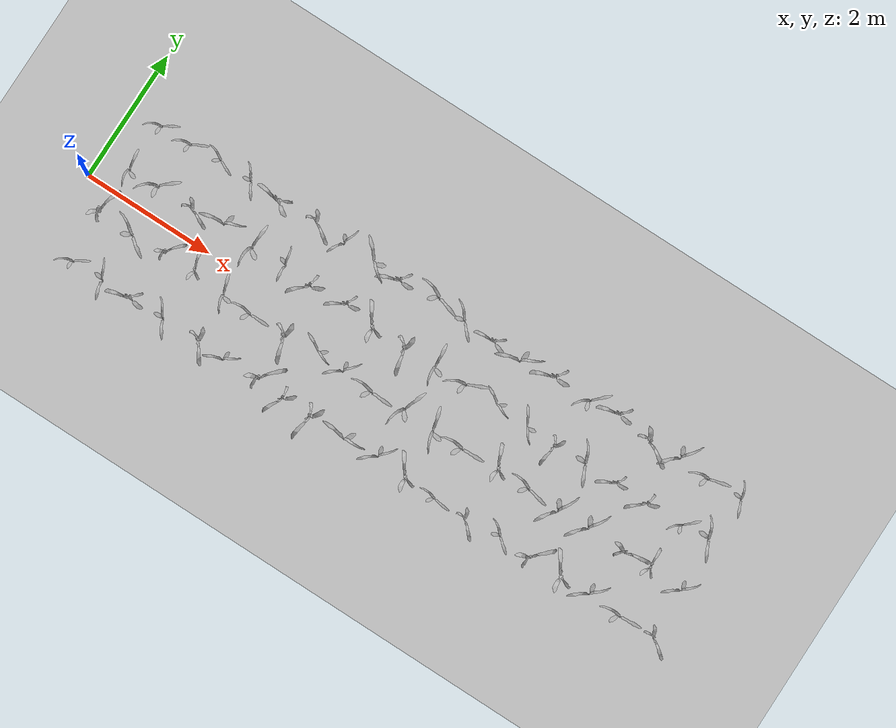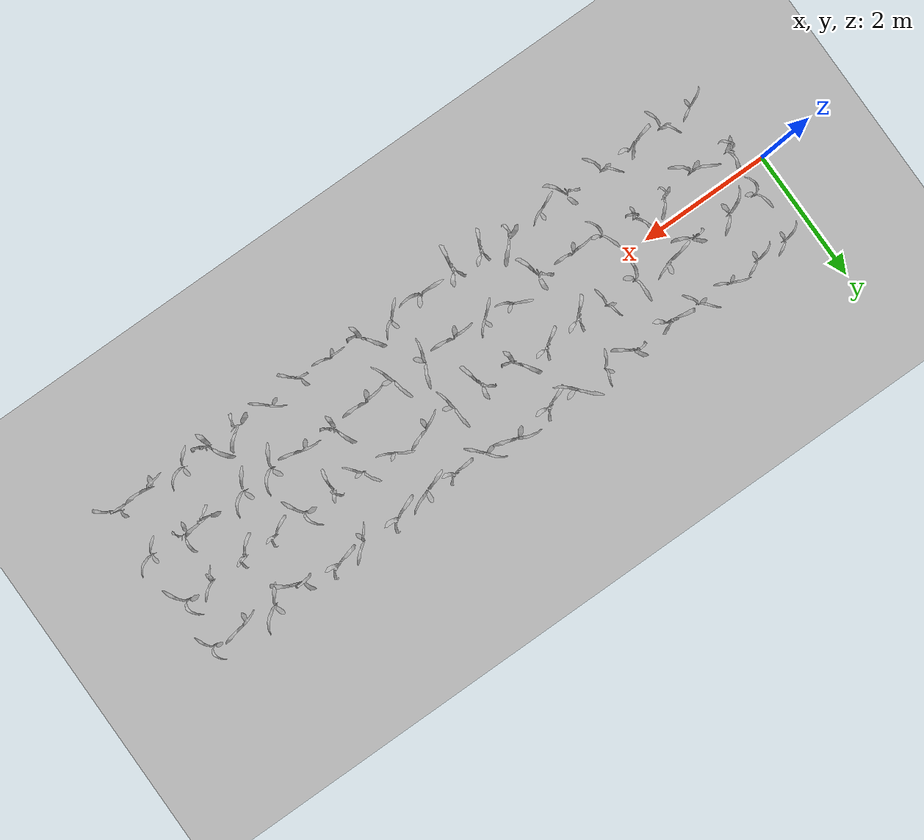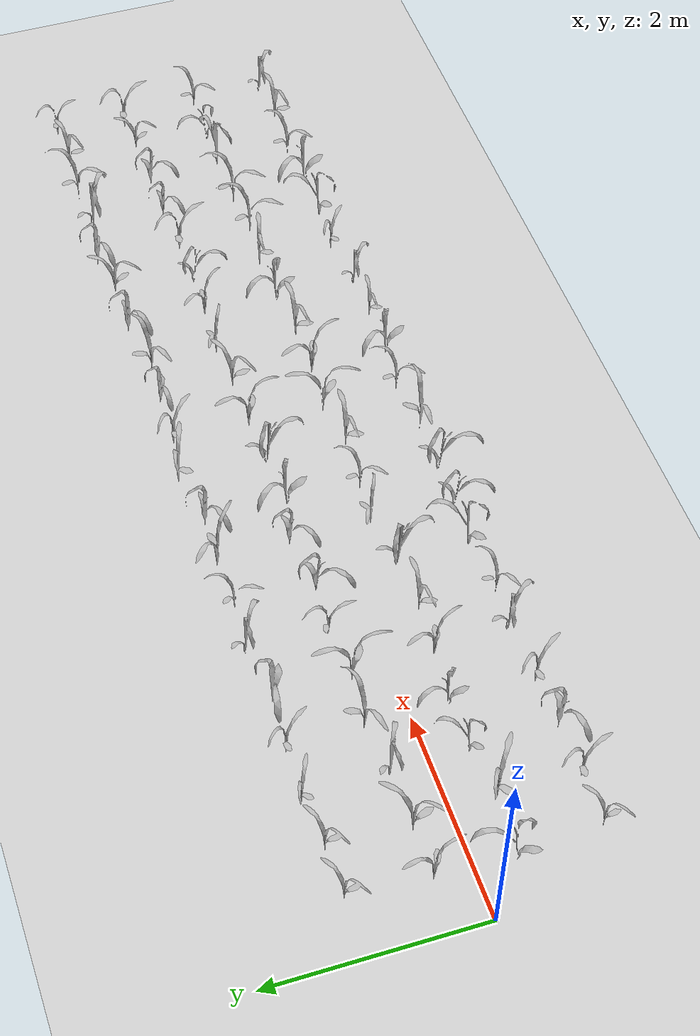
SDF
<sdf version="1.6">
 <world name="default">
  <light name="sun" type="directional">
   <pose>0 0 10 0 -0 0</pose>
   <diffuse>0.8 0.8 0.8 1</diffuse>
   <specular>0.2 0.2 0.2 1</specular>
   <attenuation>
    <range>1000</range>
    <constant>0.9</constant>
    <linear>0.01</linear>
    <quadratic>0.001</quadratic>
   </attenuation>
   <direction>-0.5 0.1 -0.9</direction>
  </light>
  <model name="ground_plane">
   <static>1</static>
   <link name="link">
    <collision name="collision">
     <geometry><plane><normal>0 0 1</normal><size>100 100</size></plane></geometry>
     <surface>
      <contact><collide_bitmask>65535</collide_bitmask></contact>
      <friction><ode><mu>100</mu><mu2>50</mu2></ode></friction>
     </surface>
    </collision>
    <visual name="visual">
     <cast_shadows>0</cast_shadows>
     <geometry><plane><normal>0 0 1</normal><size>100 100</size></plane></geometry>
     <material>
      <script><uri>file://media/materials/scripts/gazebo.material</uri><name>Gazebo/Grey</name></script>
     </material>
    </visual>
   </link>
  </model>
  <gravity>0 0 -9.8</gravity>
  <magnetic_field>6e-06 2.3e-05 -4.2e-05</magnetic_field>
  <atmosphere type="adiabatic"/>
  <physics name="default_physics" default="0" type="ode">
   <max_step_size>0.001</max_step_size>
   <real_time_factor>1</real_time_factor>
   <real_time_update_rate>1000</real_time_update_rate>
  </physics>
  <scene><ambient>0.4 0.4 0.4 1</ambient><background>0.7 0.7 0.7 1</background><shadows>1</shadows></scene>
  <audio><device>default</device></audio>
  <spherical_coordinates>
   <surface_model>EARTH_WGS84</surface_model>
   <latitude_deg>0</latitude_deg>
   <longitude_deg>0</longitude_deg>
   <elevation>0</elevation>
   <heading_deg>0</heading_deg>
  </spherical_coordinates>
  <model name="maize_02_0000">
   <pose>0.47049687635757786 0.36059624816049446 0.05 0 -0 3.884376960616973</pose>
   <link name="maize_02_0000_link">
    <inertial>
     <mass>5.0</mass>
     <inertia>
      <ixx>0.0033416667</ixx>
      <ixy>0</ixy>
      <ixz>0</ixz>
      <iyy>0.0033416667</iyy>
      <iyz>0</iyz>
      <izz>0.000016666667</izz>
     </inertia>
     <pose>0 0 0.1 0 0 0</pose>
    </inertial>
    <collision name="collision">
     <pose>0 0 0.2 0 -0 0</pose>
     <geometry><box><size>0.02 0.02 0.4</size></box></geometry>
     <surface><friction><ode><mu>10</mu><mu2>10</mu2></ode></friction></surface>
    </collision>
    <visual name="visual">
     <geometry>
      <mesh>
       <uri>model://maize_02/meshes/maize_02.dae</uri>
       <scale>0.5674274716346216 0.5674274716346216 0.5674274716346216</scale>
      </mesh>
     </geometry>
    </visual>
   </link>
  </model>
  <model name="maize_02_0001">
   <pose>0.508140931266495 1.104313894945125 0.05 0 -0 2.666948852061892</pose>
   <link name="maize_02_0001_link">
    <inertial>
     <mass>5.0</mass>
     <inertia>
      <ixx>0.0033416667</ixx>
      <ixy>0</ixy>
      <ixz>0</ixz>
      <iyy>0.0033416667</iyy>
      <iyz>0</iyz>
      <izz>0.000016666667</izz>
     </inertia>
     <pose>0 0 0.1 0 0 0</pose>
    </inertial>
    <collision name="collision">
     <pose>0 0 0.2 0 -0 0</pose>
     <geometry><box><size>0.02 0.02 0.4</size></box></geometry>
     <surface><friction><ode><mu>10</mu><mu2>10</mu2></ode></friction></surface>
    </collision>
    <visual name="visual">
     <geometry>
      <mesh>
       <uri>model://maize_02/meshes/maize_02.dae</uri>
       <scale>0.5115875292245987 0.5115875292245987 0.5115875292245987</scale>
      </mesh>
     </geometry>
    </visual>
   </link>
  </model>
  <model name="maize_01_0002">
   <pose>0.43486589940218173 -0.3454473768139016 0.05 0 -0 2.066160482995275</pose>
   <link name="maize_01_0002_link">
    <inertial>
     <mass>5.0</mass>
     <inertia>
      <ixx>0.0033416667</ixx>
      <ixy>0</ixy>
      <ixz>0</ixz>
      <iyy>0.0033416667</iyy>
      <iyz>0</iyz>
      <izz>0.000016666667</izz>
     </inertia>
     <pose>0 0 0.1 0 0 0</pose>
    </inertial>
    <collision name="collision">
     <pose>0 0 0.2 0 -0 0</pose>
     <geometry><box><size>0.02 0.02 0.4</size></box></geometry>
     <surface><friction><ode><mu>10</mu><mu2>10</mu2></ode></friction></surface>
    </collision>
    <visual name="visual">
     <geometry>
      <mesh>
       <uri>model://maize_01/meshes/maize_01.dae</uri>
       <scale>0.6489830155867166 0.6489830155867166 0.6489830155867166</scale>
      </mesh>
     </geometry>
    </visual>
   </link>
  </model>
  <model name="maize_02_0003">
   <pose>0.5099315625908049 -1.1301390917868228 0.05 0 -0 2.694714453417864</pose>
   <link name="maize_02_0003_link">
    <inertial>
     <mass>5.0</mass>
     <inertia>
      <ixx>0.0033416667</ixx>
      <ixy>0</ixy>
      <ixz>0</ixz>
      <iyy>0.0033416667</iyy>
      <iyz>0</iyz>
      <izz>0.000016666667</izz>
     </inertia>
     <pose>0 0 0.1 0 0 0</pose>
    </inertial>
    <collision name="collision">
     <pose>0 0 0.2 0 -0 0</pose>
     <geometry><box><size>0.02 0.02 0.4</size></box></geometry>
     <surface><friction><ode><mu>10</mu><mu2>10</mu2></ode></friction></surface>
    </collision>
    <visual name="visual">
     <geometry>
      <mesh>
       <uri>model://maize_02/meshes/maize_02.dae</uri>
       <scale>0.5016709728173756 0.5016709728173756 0.5016709728173756</scale>
      </mesh>
     </geometry>
    </visual>
   </link>
  </model>
  <model name="maize_02_0004">
   <pose>0.9311962609178649 0.3729072653908273 0.05 0 -0 2.855051085785902</pose>
   <link name="maize_02_0004_link">
    <inertial>
     <mass>5.0</mass>
     <inertia>
      <ixx>0.0033416667</ixx>
      <ixy>0</ixy>
      <ixz>0</ixz>
      <iyy>0.0033416667</iyy>
      <iyz>0</iyz>
      <izz>0.000016666667</izz>
     </inertia>
     <pose>0 0 0.1 0 0 0</pose>
    </inertial>
    <collision name="collision">
     <pose>0 0 0.2 0 -0 0</pose>
     <geometry><box><size>0.02 0.02 0.4</size></box></geometry>
     <surface><friction><ode><mu>10</mu><mu2>10</mu2></ode></friction></surface>
    </collision>
    <visual name="visual">
     <geometry>
      <mesh>
       <uri>model://maize_02/meshes/maize_02.dae</uri>
       <scale>0.662688299009895 0.662688299009895 0.662688299009895</scale>
      </mesh>
     </geometry>
    </visual>
   </link>
  </model>
  <model name="maize_02_0005">
   <pose>0.9833217093753088 1.109699803739185 0.05 0 -0 2.581048507436319</pose>
   <link name="maize_02_0005_link">
    <inertial>
     <mass>5.0</mass>
     <inertia>
      <ixx>0.0033416667</ixx>
      <ixy>0</ixy>
      <ixz>0</ixz>
      <iyy>0.0033416667</iyy>
      <iyz>0</iyz>
      <izz>0.000016666667</izz>
     </inertia>
     <pose>0 0 0.1 0 0 0</pose>
    </inertial>
    <collision name="collision">
     <pose>0 0 0.2 0 -0 0</pose>
     <geometry><box><size>0.02 0.02 0.4</size></box></geometry>
     <surface><friction><ode><mu>10</mu><mu2>10</mu2></ode></friction></surface>
    </collision>
    <visual name="visual">
     <geometry>
      <mesh>
       <uri>model://maize_02/meshes/maize_02.dae</uri>
       <scale>0.5312986790910379 0.5312986790910379 0.5312986790910379</scale>
      </mesh>
     </geometry>
    </visual>
   </link>
  </model>
  <model name="maize_02_0006">
   <pose>1.0187841868410517 -0.3981828536381571 0.05 0 -0 1.578195125479709</pose>
   <link name="maize_02_0006_link">
    <inertial>
     <mass>5.0</mass>
     <inertia>
      <ixx>0.0033416667</ixx>
      <ixy>0</ixy>
      <ixz>0</ixz>
      <iyy>0.0033416667</iyy>
      <iyz>0</iyz>
      <izz>0.000016666667</izz>
     </inertia>
     <pose>0 0 0.1 0 0 0</pose>
    </inertial>
    <collision name="collision">
     <pose>0 0 0.2 0 -0 0</pose>
     <geometry><box><size>0.02 0.02 0.4</size></box></geometry>
     <surface><friction><ode><mu>10</mu><mu2>10</mu2></ode></friction></surface>
    </collision>
    <visual name="visual">
     <geometry>
      <mesh>
       <uri>model://maize_02/meshes/maize_02.dae</uri>
       <scale>0.6868409701709819 0.6868409701709819 0.6868409701709819</scale>
      </mesh>
     </geometry>
    </visual>
   </link>
  </model>
  <model name="maize_02_0007">
   <pose>0.9982340490399799 -1.1398354682902523 0.05 0 -0 0.9474725027138337</pose>
   <link name="maize_02_0007_link">
    <inertial>
     <mass>5.0</mass>
     <inertia>
      <ixx>0.0033416667</ixx>
      <ixy>0</ixy>
      <ixz>0</ixz>
      <iyy>0.0033416667</iyy>
      <iyz>0</iyz>
      <izz>0.000016666667</izz>
     </inertia>
     <pose>0 0 0.1 0 0 0</pose>
    </inertial>
    <collision name="collision">
     <pose>0 0 0.2 0 -0 0</pose>
     <geometry><box><size>0.02 0.02 0.4</size></box></geometry>
     <surface><friction><ode><mu>10</mu><mu2>10</mu2></ode></friction></surface>
    </collision>
    <visual name="visual">
     <geometry>
      <mesh>
       <uri>model://maize_02/meshes/maize_02.dae</uri>
       <scale>0.5753369803053865 0.5753369803053865 0.5753369803053865</scale>
      </mesh>
     </geometry>
    </visual>
   </link>
  </model>
  <model name="maize_01_0008">
   <pose>1.4910292846520345 0.36998147962649564 0.05 0 -0 0.354033093321621</pose>
   <link name="maize_01_0008_link">
    <inertial>
     <mass>5.0</mass>
     <inertia>
      <ixx>0.0033416667</ixx>
      <ixy>0</ixy>
      <ixz>0</ixz>
      <iyy>0.0033416667</iyy>
      <iyz>0</iyz>
      <izz>0.000016666667</izz>
     </inertia>
     <pose>0 0 0.1 0 0 0</pose>
    </inertial>
    <collision name="collision">
     <pose>0 0 0.2 0 -0 0</pose>
     <geometry><box><size>0.02 0.02 0.4</size></box></geometry>
     <surface><friction><ode><mu>10</mu><mu2>10</mu2></ode></friction></surface>
    </collision>
    <visual name="visual">
     <geometry>
      <mesh>
       <uri>model://maize_01/meshes/maize_01.dae</uri>
       <scale>0.5600452258106574 0.5600452258106574 0.5600452258106574</scale>
      </mesh>
     </geometry>
    </visual>
   </link>
  </model>
  <model name="maize_02_0009">
   <pose>1.463804960982392 1.1517406796965655 0.05 0 -0 1.737335462703134</pose>
   <link name="maize_02_0009_link">
    <inertial>
     <mass>5.0</mass>
     <inertia>
      <ixx>0.0033416667</ixx>
      <ixy>0</ixy>
      <ixz>0</ixz>
      <iyy>0.0033416667</iyy>
      <iyz>0</iyz>
      <izz>0.000016666667</izz>
     </inertia>
     <pose>0 0 0.1 0 0 0</pose>
    </inertial>
    <collision name="collision">
     <pose>0 0 0.2 0 -0 0</pose>
     <geometry><box><size>0.02 0.02 0.4</size></box></geometry>
     <surface><friction><ode><mu>10</mu><mu2>10</mu2></ode></friction></surface>
    </collision>
    <visual name="visual">
     <geometry>
      <mesh>
       <uri>model://maize_02/meshes/maize_02.dae</uri>
       <scale>0.5069168064555951 0.5069168064555951 0.5069168064555951</scale>
      </mesh>
     </geometry>
    </visual>
   </link>
  </model>
  <model name="maize_01_0010">
   <pose>1.50807623899649 -0.33465844761086383 0.05 0 -0 1.6519221138219264</pose>
   <link name="maize_01_0010_link">
    <inertial>
     <mass>5.0</mass>
     <inertia>
      <ixx>0.0033416667</ixx>
      <ixy>0</ixy>
      <ixz>0</ixz>
      <iyy>0.0033416667</iyy>
      <iyz>0</iyz>
      <izz>0.000016666667</izz>
     </inertia>
     <pose>0 0 0.1 0 0 0</pose>
    </inertial>
    <collision name="collision">
     <pose>0 0 0.2 0 -0 0</pose>
     <geometry><box><size>0.02 0.02 0.4</size></box></geometry>
     <surface><friction><ode><mu>10</mu><mu2>10</mu2></ode></friction></surface>
    </collision>
    <visual name="visual">
     <geometry>
      <mesh>
       <uri>model://maize_01/meshes/maize_01.dae</uri>
       <scale>0.5238968436570051 0.5238968436570051 0.5238968436570051</scale>
      </mesh>
     </geometry>
    </visual>
   </link>
  </model>
  <model name="maize_01_0011">
   <pose>1.4978745621224943 -1.1325892652221476 0.05 0 -0 4.200214076907188</pose>
   <link name="maize_01_0011_link">
    <inertial>
     <mass>5.0</mass>
     <inertia>
      <ixx>0.0033416667</ixx>
      <ixy>0</ixy>
      <ixz>0</ixz>
      <iyy>0.0033416667</iyy>
      <iyz>0</iyz>
      <izz>0.000016666667</izz>
     </inertia>
     <pose>0 0 0.1 0 0 0</pose>
    </inertial>
    <collision name="collision">
     <pose>0 0 0.2 0 -0 0</pose>
     <geometry><box><size>0.02 0.02 0.4</size></box></geometry>
     <surface><friction><ode><mu>10</mu><mu2>10</mu2></ode></friction></surface>
    </collision>
    <visual name="visual">
     <geometry>
      <mesh>
       <uri>model://maize_01/meshes/maize_01.dae</uri>
       <scale>0.6493503078875315 0.6493503078875315 0.6493503078875315</scale>
      </mesh>
     </geometry>
    </visual>
   </link>
  </model>
  <model name="maize_02_0012">
   <pose>1.972013142105016 0.4362986354244308 0.05 0 -0 5.554065683698922</pose>
   <link name="maize_02_0012_link">
    <inertial>
     <mass>5.0</mass>
     <inertia>
      <ixx>0.0033416667</ixx>
      <ixy>0</ixy>
      <ixz>0</ixz>
      <iyy>0.0033416667</iyy>
      <iyz>0</iyz>
      <izz>0.000016666667</izz>
     </inertia>
     <pose>0 0 0.1 0 0 0</pose>
    </inertial>
    <collision name="collision">
     <pose>0 0 0.2 0 -0 0</pose>
     <geometry><box><size>0.02 0.02 0.4</size></box></geometry>
     <surface><friction><ode><mu>10</mu><mu2>10</mu2></ode></friction></surface>
    </collision>
    <visual name="visual">
     <geometry>
      <mesh>
       <uri>model://maize_02/meshes/maize_02.dae</uri>
       <scale>0.6814321854556409 0.6814321854556409 0.6814321854556409</scale>
      </mesh>
     </geometry>
    </visual>
   </link>
  </model>
  <model name="maize_02_0013">
   <pose>1.9722264010497819 1.1272146396033693 0.05 0 -0 1.2048861847161072</pose>
   <link name="maize_02_0013_link">
    <inertial>
     <mass>5.0</mass>
     <inertia>
      <ixx>0.0033416667</ixx>
      <ixy>0</ixy>
      <ixz>0</ixz>
      <iyy>0.0033416667</iyy>
      <iyz>0</iyz>
      <izz>0.000016666667</izz>
     </inertia>
     <pose>0 0 0.1 0 0 0</pose>
    </inertial>
    <collision name="collision">
     <pose>0 0 0.2 0 -0 0</pose>
     <geometry><box><size>0.02 0.02 0.4</size></box></geometry>
     <surface><friction><ode><mu>10</mu><mu2>10</mu2></ode></friction></surface>
    </collision>
    <visual name="visual">
     <geometry>
      <mesh>
       <uri>model://maize_02/meshes/maize_02.dae</uri>
       <scale>0.5304891759352847 0.5304891759352847 0.5304891759352847</scale>
      </mesh>
     </geometry>
    </visual>
   </link>
  </model>
  <model name="maize_01_0014">
   <pose>1.9960204431345903 -0.3313790354089761 0.05 0 -0 2.630277585510729</pose>
   <link name="maize_01_0014_link">
    <inertial>
     <mass>5.0</mass>
     <inertia>
      <ixx>0.0033416667</ixx>
      <ixy>0</ixy>
      <ixz>0</ixz>
      <iyy>0.0033416667</iyy>
      <iyz>0</iyz>
      <izz>0.000016666667</izz>
     </inertia>
     <pose>0 0 0.1 0 0 0</pose>
    </inertial>
    <collision name="collision">
     <pose>0 0 0.2 0 -0 0</pose>
     <geometry><box><size>0.02 0.02 0.4</size></box></geometry>
     <surface><friction><ode><mu>10</mu><mu2>10</mu2></ode></friction></surface>
    </collision>
    <visual name="visual">
     <geometry>
      <mesh>
       <uri>model://maize_01/meshes/maize_01.dae</uri>
       <scale>0.5538803203068241 0.5538803203068241 0.5538803203068241</scale>
      </mesh>
     </geometry>
    </visual>
   </link>
  </model>
  <model name="maize_02_0015">
   <pose>1.9959096789572015 -1.129340379910915 0.05 0 -0 1.172286415792516</pose>
   <link name="maize_02_0015_link">
    <inertial>
     <mass>5.0</mass>
     <inertia>
      <ixx>0.0033416667</ixx>
      <ixy>0</ixy>
      <ixz>0</ixz>
      <iyy>0.0033416667</iyy>
      <iyz>0</iyz>
      <izz>0.000016666667</izz>
     </inertia>
     <pose>0 0 0.1 0 0 0</pose>
    </inertial>
    <collision name="collision">
     <pose>0 0 0.2 0 -0 0</pose>
     <geometry><box><size>0.02 0.02 0.4</size></box></geometry>
     <surface><friction><ode><mu>10</mu><mu2>10</mu2></ode></friction></surface>
    </collision>
    <visual name="visual">
     <geometry>
      <mesh>
       <uri>model://maize_02/meshes/maize_02.dae</uri>
       <scale>0.5845602602874503 0.5845602602874503 0.5845602602874503</scale>
      </mesh>
     </geometry>
    </visual>
   </link>
  </model>
  <model name="maize_02_0016">
   <pose>2.4899421607883987 0.36773069705212297 0.05 0 -0 3.6724743535783757</pose>
   <link name="maize_02_0016_link">
    <inertial>
     <mass>5.0</mass>
     <inertia>
      <ixx>0.0033416667</ixx>
      <ixy>0</ixy>
      <ixz>0</ixz>
      <iyy>0.0033416667</iyy>
      <iyz>0</iyz>
      <izz>0.000016666667</izz>
     </inertia>
     <pose>0 0 0.1 0 0 0</pose>
    </inertial>
    <collision name="collision">
     <pose>0 0 0.2 0 -0 0</pose>
     <geometry><box><size>0.02 0.02 0.4</size></box></geometry>
     <surface><friction><ode><mu>10</mu><mu2>10</mu2></ode></friction></surface>
    </collision>
    <visual name="visual">
     <geometry>
      <mesh>
       <uri>model://maize_02/meshes/maize_02.dae</uri>
       <scale>0.6978009730400911 0.6978009730400911 0.6978009730400911</scale>
      </mesh>
     </geometry>
    </visual>
   </link>
  </model>
  <model name="maize_01_0017">
   <pose>2.4798370892079538 1.0891925927552135 0.05 0 -0 3.772195409406952</pose>
   <link name="maize_01_0017_link">
    <inertial>
     <mass>5.0</mass>
     <inertia>
      <ixx>0.0033416667</ixx>
      <ixy>0</ixy>
      <ixz>0</ixz>
      <iyy>0.0033416667</iyy>
      <iyz>0</iyz>
      <izz>0.000016666667</izz>
     </inertia>
     <pose>0 0 0.1 0 0 0</pose>
    </inertial>
    <collision name="collision">
     <pose>0 0 0.2 0 -0 0</pose>
     <geometry><box><size>0.02 0.02 0.4</size></box></geometry>
     <surface><friction><ode><mu>10</mu><mu2>10</mu2></ode></friction></surface>
    </collision>
    <visual name="visual">
     <geometry>
      <mesh>
       <uri>model://maize_01/meshes/maize_01.dae</uri>
       <scale>0.6694863712459956 0.6694863712459956 0.6694863712459956</scale>
      </mesh>
     </geometry>
    </visual>
   </link>
  </model>
  <model name="maize_02_0018">
   <pose>2.5130626953292317 -0.3907262505887491 0.05 0 -0 4.057416928748751</pose>
   <link name="maize_02_0018_link">
    <inertial>
     <mass>5.0</mass>
     <inertia>
      <ixx>0.0033416667</ixx>
      <ixy>0</ixy>
      <ixz>0</ixz>
      <iyy>0.0033416667</iyy>
      <iyz>0</iyz>
      <izz>0.000016666667</izz>
     </inertia>
     <pose>0 0 0.1 0 0 0</pose>
    </inertial>
    <collision name="collision">
     <pose>0 0 0.2 0 -0 0</pose>
     <geometry><box><size>0.02 0.02 0.4</size></box></geometry>
     <surface><friction><ode><mu>10</mu><mu2>10</mu2></ode></friction></surface>
    </collision>
    <visual name="visual">
     <geometry>
      <mesh>
       <uri>model://maize_02/meshes/maize_02.dae</uri>
       <scale>0.5874464423976106 0.5874464423976106 0.5874464423976106</scale>
      </mesh>
     </geometry>
    </visual>
   </link>
  </model>
  <model name="maize_01_0019">
   <pose>2.565462817772224 -1.0988761495902357 0.05 0 -0 6.128877144391759</pose>
   <link name="maize_01_0019_link">
    <inertial>
     <mass>5.0</mass>
     <inertia>
      <ixx>0.0033416667</ixx>
      <ixy>0</ixy>
      <ixz>0</ixz>
      <iyy>0.0033416667</iyy>
      <iyz>0</iyz>
      <izz>0.000016666667</izz>
     </inertia>
     <pose>0 0 0.1 0 0 0</pose>
    </inertial>
    <collision name="collision">
     <pose>0 0 0.2 0 -0 0</pose>
     <geometry><box><size>0.02 0.02 0.4</size></box></geometry>
     <surface><friction><ode><mu>10</mu><mu2>10</mu2></ode></friction></surface>
    </collision>
    <visual name="visual">
     <geometry>
      <mesh>
       <uri>model://maize_01/meshes/maize_01.dae</uri>
       <scale>0.6065098796899253 0.6065098796899253 0.6065098796899253</scale>
      </mesh>
     </geometry>
    </visual>
   </link>
  </model>
  <model name="maize_02_0020">
   <pose>3.0013577122880113 0.41387817632451973 0.05 0 -0 0.7418947153538963</pose>
   <link name="maize_02_0020_link">
    <inertial>
     <mass>5.0</mass>
     <inertia>
      <ixx>0.0033416667</ixx>
      <ixy>0</ixy>
      <ixz>0</ixz>
      <iyy>0.0033416667</iyy>
      <iyz>0</iyz>
      <izz>0.000016666667</izz>
     </inertia>
     <pose>0 0 0.1 0 0 0</pose>
    </inertial>
    <collision name="collision">
     <pose>0 0 0.2 0 -0 0</pose>
     <geometry><box><size>0.02 0.02 0.4</size></box></geometry>
     <surface><friction><ode><mu>10</mu><mu2>10</mu2></ode></friction></surface>
    </collision>
    <visual name="visual">
     <geometry>
      <mesh>
       <uri>model://maize_02/meshes/maize_02.dae</uri>
       <scale>0.514632109587351 0.514632109587351 0.514632109587351</scale>
      </mesh>
     </geometry>
    </visual>
   </link>
  </model>
  <model name="maize_01_0021">
   <pose>3.032986096075952 1.156134638640285 0.05 0 -0 0.1977341317002129</pose>
   <link name="maize_01_0021_link">
    <inertial>
     <mass>5.0</mass>
     <inertia>
      <ixx>0.0033416667</ixx>
      <ixy>0</ixy>
      <ixz>0</ixz>
      <iyy>0.0033416667</iyy>
      <iyz>0</iyz>
      <izz>0.000016666667</izz>
     </inertia>
     <pose>0 0 0.1 0 0 0</pose>
    </inertial>
    <collision name="collision">
     <pose>0 0 0.2 0 -0 0</pose>
     <geometry><box><size>0.02 0.02 0.4</size></box></geometry>
     <surface><friction><ode><mu>10</mu><mu2>10</mu2></ode></friction></surface>
    </collision>
    <visual name="visual">
     <geometry>
      <mesh>
       <uri>model://maize_01/meshes/maize_01.dae</uri>
       <scale>0.5876208934212445 0.5876208934212445 0.5876208934212445</scale>
      </mesh>
     </geometry>
    </visual>
   </link>
  </model>
  <model name="maize_02_0022">
   <pose>2.9804407283532983 -0.42109649388774395 0.05 0 -0 2.155444909990796</pose>
   <link name="maize_02_0022_link">
    <inertial>
     <mass>5.0</mass>
     <inertia>
      <ixx>0.0033416667</ixx>
      <ixy>0</ixy>
      <ixz>0</ixz>
      <iyy>0.0033416667</iyy>
      <iyz>0</iyz>
      <izz>0.000016666667</izz>
     </inertia>
     <pose>0 0 0.1 0 0 0</pose>
    </inertial>
    <collision name="collision">
     <pose>0 0 0.2 0 -0 0</pose>
     <geometry><box><size>0.02 0.02 0.4</size></box></geometry>
     <surface><friction><ode><mu>10</mu><mu2>10</mu2></ode></friction></surface>
    </collision>
    <visual name="visual">
     <geometry>
      <mesh>
       <uri>model://maize_02/meshes/maize_02.dae</uri>
       <scale>0.6079977954316437 0.6079977954316437 0.6079977954316437</scale>
      </mesh>
     </geometry>
    </visual>
   </link>
  </model>
  <model name="maize_02_0023">
   <pose>2.9859502665502844 -1.145055179218194 0.05 0 -0 5.758024759081069</pose>
   <link name="maize_02_0023_link">
    <inertial>
     <mass>5.0</mass>
     <inertia>
      <ixx>0.0033416667</ixx>
      <ixy>0</ixy>
      <ixz>0</ixz>
      <iyy>0.0033416667</iyy>
      <iyz>0</iyz>
      <izz>0.000016666667</izz>
     </inertia>
     <pose>0 0 0.1 0 0 0</pose>
    </inertial>
    <collision name="collision">
     <pose>0 0 0.2 0 -0 0</pose>
     <geometry><box><size>0.02 0.02 0.4</size></box></geometry>
     <surface><friction><ode><mu>10</mu><mu2>10</mu2></ode></friction></surface>
    </collision>
    <visual name="visual">
     <geometry>
      <mesh>
       <uri>model://maize_02/meshes/maize_02.dae</uri>
       <scale>0.533953348824247 0.533953348824247 0.533953348824247</scale>
      </mesh>
     </geometry>
    </visual>
   </link>
  </model>
  <model name="maize_01_0024">
   <pose>3.4705427651438834 0.37124192825648084 0.05 0 -0 4.737169701775158</pose>
   <link name="maize_01_0024_link">
    <inertial>
     <mass>5.0</mass>
     <inertia>
      <ixx>0.0033416667</ixx>
      <ixy>0</ixy>
      <ixz>0</ixz>
      <iyy>0.0033416667</iyy>
      <iyz>0</iyz>
      <izz>0.000016666667</izz>
     </inertia>
     <pose>0 0 0.1 0 0 0</pose>
    </inertial>
    <collision name="collision">
     <pose>0 0 0.2 0 -0 0</pose>
     <geometry><box><size>0.02 0.02 0.4</size></box></geometry>
     <surface><friction><ode><mu>10</mu><mu2>10</mu2></ode></friction></surface>
    </collision>
    <visual name="visual">
     <geometry>
      <mesh>
       <uri>model://maize_01/meshes/maize_01.dae</uri>
       <scale>0.6189004155222745 0.6189004155222745 0.6189004155222745</scale>
      </mesh>
     </geometry>
    </visual>
   </link>
  </model>
  <model name="maize_02_0025">
   <pose>3.51355015213579 1.1123997917842876 0.05 0 -0 0.14389386696007964</pose>
   <link name="maize_02_0025_link">
    <inertial>
     <mass>5.0</mass>
     <inertia>
      <ixx>0.0033416667</ixx>
      <ixy>0</ixy>
      <ixz>0</ixz>
      <iyy>0.0033416667</iyy>
      <iyz>0</iyz>
      <izz>0.000016666667</izz>
     </inertia>
     <pose>0 0 0.1 0 0 0</pose>
    </inertial>
    <collision name="collision">
     <pose>0 0 0.2 0 -0 0</pose>
     <geometry><box><size>0.02 0.02 0.4</size></box></geometry>
     <surface><friction><ode><mu>10</mu><mu2>10</mu2></ode></friction></surface>
    </collision>
    <visual name="visual">
     <geometry>
      <mesh>
       <uri>model://maize_02/meshes/maize_02.dae</uri>
       <scale>0.5227514900756978 0.5227514900756978 0.5227514900756978</scale>
      </mesh>
     </geometry>
    </visual>
   </link>
  </model>
  <model name="maize_01_0026">
   <pose>3.5254951566729456 -0.40938334789493747 0.05 0 -0 5.832737683356969</pose>
   <link name="maize_01_0026_link">
    <inertial>
     <mass>5.0</mass>
     <inertia>
      <ixx>0.0033416667</ixx>
      <ixy>0</ixy>
      <ixz>0</ixz>
      <iyy>0.0033416667</iyy>
      <iyz>0</iyz>
      <izz>0.000016666667</izz>
     </inertia>
     <pose>0 0 0.1 0 0 0</pose>
    </inertial>
    <collision name="collision">
     <pose>0 0 0.2 0 -0 0</pose>
     <geometry><box><size>0.02 0.02 0.4</size></box></geometry>
     <surface><friction><ode><mu>10</mu><mu2>10</mu2></ode></friction></surface>
    </collision>
    <visual name="visual">
     <geometry>
      <mesh>
       <uri>model://maize_01/meshes/maize_01.dae</uri>
       <scale>0.679571244358817 0.679571244358817 0.679571244358817</scale>
      </mesh>
     </geometry>
    </visual>
   </link>
  </model>
  <model name="maize_01_0027">
   <pose>3.551398597729426 -1.098131697571287 0.05 0 -0 1.613967359752651</pose>
   <link name="maize_01_0027_link">
    <inertial>
     <mass>5.0</mass>
     <inertia>
      <ixx>0.0033416667</ixx>
      <ixy>0</ixy>
      <ixz>0</ixz>
      <iyy>0.0033416667</iyy>
      <iyz>0</iyz>
      <izz>0.000016666667</izz>
     </inertia>
     <pose>0 0 0.1 0 0 0</pose>
    </inertial>
    <collision name="collision">
     <pose>0 0 0.2 0 -0 0</pose>
     <geometry><box><size>0.02 0.02 0.4</size></box></geometry>
     <surface><friction><ode><mu>10</mu><mu2>10</mu2></ode></friction></surface>
    </collision>
    <visual name="visual">
     <geometry>
      <mesh>
       <uri>model://maize_01/meshes/maize_01.dae</uri>
       <scale>0.6787900228724834 0.6787900228724834 0.6787900228724834</scale>
      </mesh>
     </geometry>
    </visual>
   </link>
  </model>
  <model name="maize_01_0028">
   <pose>4.038935901359413 0.43676302517460464 0.05 0 -0 4.505408310408163</pose>
   <link name="maize_01_0028_link">
    <inertial>
     <mass>5.0</mass>
     <inertia>
      <ixx>0.0033416667</ixx>
      <ixy>0</ixy>
      <ixz>0</ixz>
      <iyy>0.0033416667</iyy>
      <iyz>0</iyz>
      <izz>0.000016666667</izz>
     </inertia>
     <pose>0 0 0.1 0 0 0</pose>
    </inertial>
    <collision name="collision">
     <pose>0 0 0.2 0 -0 0</pose>
     <geometry><box><size>0.02 0.02 0.4</size></box></geometry>
     <surface><friction><ode><mu>10</mu><mu2>10</mu2></ode></friction></surface>
    </collision>
    <visual name="visual">
     <geometry>
      <mesh>
       <uri>model://maize_01/meshes/maize_01.dae</uri>
       <scale>0.5771859699419091 0.5771859699419091 0.5771859699419091</scale>
      </mesh>
     </geometry>
    </visual>
   </link>
  </model>
  <model name="maize_02_0029">
   <pose>4.009812641180788 1.1255841615126954 0.05 0 -0 4.533838017147104</pose>
   <link name="maize_02_0029_link">
    <inertial>
     <mass>5.0</mass>
     <inertia>
      <ixx>0.0033416667</ixx>
      <ixy>0</ixy>
      <ixz>0</ixz>
      <iyy>0.0033416667</iyy>
      <iyz>0</iyz>
      <izz>0.000016666667</izz>
     </inertia>
     <pose>0 0 0.1 0 0 0</pose>
    </inertial>
    <collision name="collision">
     <pose>0 0 0.2 0 -0 0</pose>
     <geometry><box><size>0.02 0.02 0.4</size></box></geometry>
     <surface><friction><ode><mu>10</mu><mu2>10</mu2></ode></friction></surface>
    </collision>
    <visual name="visual">
     <geometry>
      <mesh>
       <uri>model://maize_02/meshes/maize_02.dae</uri>
       <scale>0.6824782738088802 0.6824782738088802 0.6824782738088802</scale>
      </mesh>
     </geometry>
    </visual>
   </link>
  </model>
  <model name="maize_02_0030">
   <pose>4.0348752667196 -0.3311524043415686 0.05 0 -0 4.857825403753622</pose>
   <link name="maize_02_0030_link">
    <inertial>
     <mass>5.0</mass>
     <inertia>
      <ixx>0.0033416667</ixx>
      <ixy>0</ixy>
      <ixz>0</ixz>
      <iyy>0.0033416667</iyy>
      <iyz>0</iyz>
      <izz>0.000016666667</izz>
     </inertia>
     <pose>0 0 0.1 0 0 0</pose>
    </inertial>
    <collision name="collision">
     <pose>0 0 0.2 0 -0 0</pose>
     <geometry><box><size>0.02 0.02 0.4</size></box></geometry>
     <surface><friction><ode><mu>10</mu><mu2>10</mu2></ode></friction></surface>
    </collision>
    <visual name="visual">
     <geometry>
      <mesh>
       <uri>model://maize_02/meshes/maize_02.dae</uri>
       <scale>0.5345925895765861 0.5345925895765861 0.5345925895765861</scale>
      </mesh>
     </geometry>
    </visual>
   </link>
  </model>
  <model name="maize_01_0031">
   <pose>3.9986258673558384 -1.131019786122446 0.05 0 -0 5.0650412360898756</pose>
   <link name="maize_01_0031_link">
    <inertial>
     <mass>5.0</mass>
     <inertia>
      <ixx>0.0033416667</ixx>
      <ixy>0</ixy>
      <ixz>0</ixz>
      <iyy>0.0033416667</iyy>
      <iyz>0</iyz>
      <izz>0.000016666667</izz>
     </inertia>
     <pose>0 0 0.1 0 0 0</pose>
    </inertial>
    <collision name="collision">
     <pose>0 0 0.2 0 -0 0</pose>
     <geometry><box><size>0.02 0.02 0.4</size></box></geometry>
     <surface><friction><ode><mu>10</mu><mu2>10</mu2></ode></friction></surface>
    </collision>
    <visual name="visual">
     <geometry>
      <mesh>
       <uri>model://maize_01/meshes/maize_01.dae</uri>
       <scale>0.586369662920548 0.586369662920548 0.586369662920548</scale>
      </mesh>
     </geometry>
    </visual>
   </link>
  </model>
  <model name="maize_01_0032">
   <pose>4.494411528204541 0.3188684412651709 0.05 0 -0 2.945612463472695</pose>
   <link name="maize_01_0032_link">
    <inertial>
     <mass>5.0</mass>
     <inertia>
      <ixx>0.0033416667</ixx>
      <ixy>0</ixy>
      <ixz>0</ixz>
      <iyy>0.0033416667</iyy>
      <iyz>0</iyz>
      <izz>0.000016666667</izz>
     </inertia>
     <pose>0 0 0.1 0 0 0</pose>
    </inertial>
    <collision name="collision">
     <pose>0 0 0.2 0 -0 0</pose>
     <geometry><box><size>0.02 0.02 0.4</size></box></geometry>
     <surface><friction><ode><mu>10</mu><mu2>10</mu2></ode></friction></surface>
    </collision>
    <visual name="visual">
     <geometry>
      <mesh>
       <uri>model://maize_01/meshes/maize_01.dae</uri>
       <scale>0.6729138496896988 0.6729138496896988 0.6729138496896988</scale>
      </mesh>
     </geometry>
    </visual>
   </link>
  </model>
  <model name="maize_01_0033">
   <pose>4.481704221677015 1.1048405260704386 0.05 0 -0 4.318497426130881</pose>
   <link name="maize_01_0033_link">
    <inertial>
     <mass>5.0</mass>
     <inertia>
      <ixx>0.0033416667</ixx>
      <ixy>0</ixy>
      <ixz>0</ixz>
      <iyy>0.0033416667</iyy>
      <iyz>0</iyz>
      <izz>0.000016666667</izz>
     </inertia>
     <pose>0 0 0.1 0 0 0</pose>
    </inertial>
    <collision name="collision">
     <pose>0 0 0.2 0 -0 0</pose>
     <geometry><box><size>0.02 0.02 0.4</size></box></geometry>
     <surface><friction><ode><mu>10</mu><mu2>10</mu2></ode></friction></surface>
    </collision>
    <visual name="visual">
     <geometry>
      <mesh>
       <uri>model://maize_01/meshes/maize_01.dae</uri>
       <scale>0.6289584406914008 0.6289584406914008 0.6289584406914008</scale>
      </mesh>
     </geometry>
    </visual>
   </link>
  </model>
  <model name="maize_02_0034">
   <pose>4.468238910624119 -0.3792912988688344 0.05 0 -0 6.073926664607151</pose>
   <link name="maize_02_0034_link">
    <inertial>
     <mass>5.0</mass>
     <inertia>
      <ixx>0.0033416667</ixx>
      <ixy>0</ixy>
      <ixz>0</ixz>
      <iyy>0.0033416667</iyy>
      <iyz>0</iyz>
      <izz>0.000016666667</izz>
     </inertia>
     <pose>0 0 0.1 0 0 0</pose>
    </inertial>
    <collision name="collision">
     <pose>0 0 0.2 0 -0 0</pose>
     <geometry><box><size>0.02 0.02 0.4</size></box></geometry>
     <surface><friction><ode><mu>10</mu><mu2>10</mu2></ode></friction></surface>
    </collision>
    <visual name="visual">
     <geometry>
      <mesh>
       <uri>model://maize_02/meshes/maize_02.dae</uri>
       <scale>0.5528094305392898 0.5528094305392898 0.5528094305392898</scale>
      </mesh>
     </geometry>
    </visual>
   </link>
  </model>
  <model name="maize_01_0035">
   <pose>4.446875384365773 -1.1407014834971003 0.05 0 -0 5.351995299100307</pose>
   <link name="maize_01_0035_link">
    <inertial>
     <mass>5.0</mass>
     <inertia>
      <ixx>0.0033416667</ixx>
      <ixy>0</ixy>
      <ixz>0</ixz>
      <iyy>0.0033416667</iyy>
      <iyz>0</iyz>
      <izz>0.000016666667</izz>
     </inertia>
     <pose>0 0 0.1 0 0 0</pose>
    </inertial>
    <collision name="collision">
     <pose>0 0 0.2 0 -0 0</pose>
     <geometry><box><size>0.02 0.02 0.4</size></box></geometry>
     <surface><friction><ode><mu>10</mu><mu2>10</mu2></ode></friction></surface>
    </collision>
    <visual name="visual">
     <geometry>
      <mesh>
       <uri>model://maize_01/meshes/maize_01.dae</uri>
       <scale>0.675906921977078 0.675906921977078 0.675906921977078</scale>
      </mesh>
     </geometry>
    </visual>
   </link>
  </model>
  <model name="maize_01_0036">
   <pose>5.013109399768455 0.3470658769002186 0.05 0 -0 5.754867637289687</pose>
   <link name="maize_01_0036_link">
    <inertial>
     <mass>5.0</mass>
     <inertia>
      <ixx>0.0033416667</ixx>
      <ixy>0</ixy>
      <ixz>0</ixz>
      <iyy>0.0033416667</iyy>
      <iyz>0</iyz>
      <izz>0.000016666667</izz>
     </inertia>
     <pose>0 0 0.1 0 0 0</pose>
    </inertial>
    <collision name="collision">
     <pose>0 0 0.2 0 -0 0</pose>
     <geometry><box><size>0.02 0.02 0.4</size></box></geometry>
     <surface><friction><ode><mu>10</mu><mu2>10</mu2></ode></friction></surface>
    </collision>
    <visual name="visual">
     <geometry>
      <mesh>
       <uri>model://maize_01/meshes/maize_01.dae</uri>
       <scale>0.6676630052171705 0.6676630052171705 0.6676630052171705</scale>
      </mesh>
     </geometry>
    </visual>
   </link>
  </model>
  <model name="maize_02_0037">
   <pose>5.04050455921257 1.1898631053769173 0.05 0 -0 1.8605534795568581</pose>
   <link name="maize_02_0037_link">
    <inertial>
     <mass>5.0</mass>
     <inertia>
      <ixx>0.0033416667</ixx>
      <ixy>0</ixy>
      <ixz>0</ixz>
      <iyy>0.0033416667</iyy>
      <iyz>0</iyz>
      <izz>0.000016666667</izz>
     </inertia>
     <pose>0 0 0.1 0 0 0</pose>
    </inertial>
    <collision name="collision">
     <pose>0 0 0.2 0 -0 0</pose>
     <geometry><box><size>0.02 0.02 0.4</size></box></geometry>
     <surface><friction><ode><mu>10</mu><mu2>10</mu2></ode></friction></surface>
    </collision>
    <visual name="visual">
     <geometry>
      <mesh>
       <uri>model://maize_02/meshes/maize_02.dae</uri>
       <scale>0.6757560835256996 0.6757560835256996 0.6757560835256996</scale>
      </mesh>
     </geometry>
    </visual>
   </link>
  </model>
  <model name="maize_02_0038">
   <pose>4.972205739177155 -0.41432018499572293 0.05 0 -0 2.10815389910329</pose>
   <link name="maize_02_0038_link">
    <inertial>
     <mass>5.0</mass>
     <inertia>
      <ixx>0.0033416667</ixx>
      <ixy>0</ixy>
      <ixz>0</ixz>
      <iyy>0.0033416667</iyy>
      <iyz>0</iyz>
      <izz>0.000016666667</izz>
     </inertia>
     <pose>0 0 0.1 0 0 0</pose>
    </inertial>
    <collision name="collision">
     <pose>0 0 0.2 0 -0 0</pose>
     <geometry><box><size>0.02 0.02 0.4</size></box></geometry>
     <surface><friction><ode><mu>10</mu><mu2>10</mu2></ode></friction></surface>
    </collision>
    <visual name="visual">
     <geometry>
      <mesh>
       <uri>model://maize_02/meshes/maize_02.dae</uri>
       <scale>0.6611868578351846 0.6611868578351846 0.6611868578351846</scale>
      </mesh>
     </geometry>
    </visual>
   </link>
  </model>
  <model name="maize_02_0039">
   <pose>4.9833682163221 -1.1506723377802597 0.05 0 -0 5.247131645449195</pose>
   <link name="maize_02_0039_link">
    <inertial>
     <mass>5.0</mass>
     <inertia>
      <ixx>0.0033416667</ixx>
      <ixy>0</ixy>
      <ixz>0</ixz>
      <iyy>0.0033416667</iyy>
      <iyz>0</iyz>
      <izz>0.000016666667</izz>
     </inertia>
     <pose>0 0 0.1 0 0 0</pose>
    </inertial>
    <collision name="collision">
     <pose>0 0 0.2 0 -0 0</pose>
     <geometry><box><size>0.02 0.02 0.4</size></box></geometry>
     <surface><friction><ode><mu>10</mu><mu2>10</mu2></ode></friction></surface>
    </collision>
    <visual name="visual">
     <geometry>
      <mesh>
       <uri>model://maize_02/meshes/maize_02.dae</uri>
       <scale>0.6895169509827215 0.6895169509827215 0.6895169509827215</scale>
      </mesh>
     </geometry>
    </visual>
   </link>
  </model>
  <model name="maize_02_0040">
   <pose>5.508538671722176 0.37122853467536077 0.05 0 -0 3.8519791514515536</pose>
   <link name="maize_02_0040_link">
    <inertial>
     <mass>5.0</mass>
     <inertia>
      <ixx>0.0033416667</ixx>
      <ixy>0</ixy>
      <ixz>0</ixz>
      <iyy>0.0033416667</iyy>
      <iyz>0</iyz>
      <izz>0.000016666667</izz>
     </inertia>
     <pose>0 0 0.1 0 0 0</pose>
    </inertial>
    <collision name="collision">
     <pose>0 0 0.2 0 -0 0</pose>
     <geometry><box><size>0.02 0.02 0.4</size></box></geometry>
     <surface><friction><ode><mu>10</mu><mu2>10</mu2></ode></friction></surface>
    </collision>
    <visual name="visual">
     <geometry>
      <mesh>
       <uri>model://maize_02/meshes/maize_02.dae</uri>
       <scale>0.6436153860965608 0.6436153860965608 0.6436153860965608</scale>
      </mesh>
     </geometry>
    </visual>
   </link>
  </model>
  <model name="maize_02_0041">
   <pose>5.508247634537746 1.1057725086224237 0.05 0 -0 1.3656492372692546</pose>
   <link name="maize_02_0041_link">
    <inertial>
     <mass>5.0</mass>
     <inertia>
      <ixx>0.0033416667</ixx>
      <ixy>0</ixy>
      <ixz>0</ixz>
      <iyy>0.0033416667</iyy>
      <iyz>0</iyz>
      <izz>0.000016666667</izz>
     </inertia>
     <pose>0 0 0.1 0 0 0</pose>
    </inertial>
    <collision name="collision">
     <pose>0 0 0.2 0 -0 0</pose>
     <geometry><box><size>0.02 0.02 0.4</size></box></geometry>
     <surface><friction><ode><mu>10</mu><mu2>10</mu2></ode></friction></surface>
    </collision>
    <visual name="visual">
     <geometry>
      <mesh>
       <uri>model://maize_02/meshes/maize_02.dae</uri>
       <scale>0.5968904333593144 0.5968904333593144 0.5968904333593144</scale>
      </mesh>
     </geometry>
    </visual>
   </link>
  </model>
  <model name="maize_02_0042">
   <pose>5.477564712540988 -0.3549859986503485 0.05 0 -0 3.381817545741341</pose>
   <link name="maize_02_0042_link">
    <inertial>
     <mass>5.0</mass>
     <inertia>
      <ixx>0.0033416667</ixx>
      <ixy>0</ixy>
      <ixz>0</ixz>
      <iyy>0.0033416667</iyy>
      <iyz>0</iyz>
      <izz>0.000016666667</izz>
     </inertia>
     <pose>0 0 0.1 0 0 0</pose>
    </inertial>
    <collision name="collision">
     <pose>0 0 0.2 0 -0 0</pose>
     <geometry><box><size>0.02 0.02 0.4</size></box></geometry>
     <surface><friction><ode><mu>10</mu><mu2>10</mu2></ode></friction></surface>
    </collision>
    <visual name="visual">
     <geometry>
      <mesh>
       <uri>model://maize_02/meshes/maize_02.dae</uri>
       <scale>0.6898692024972355 0.6898692024972355 0.6898692024972355</scale>
      </mesh>
     </geometry>
    </visual>
   </link>
  </model>
  <model name="maize_02_0043">
   <pose>5.513753535963712 -1.1026228524331758 0.05 0 -0 6.090240031902223</pose>
   <link name="maize_02_0043_link">
    <inertial>
     <mass>5.0</mass>
     <inertia>
      <ixx>0.0033416667</ixx>
      <ixy>0</ixy>
      <ixz>0</ixz>
      <iyy>0.0033416667</iyy>
      <iyz>0</iyz>
      <izz>0.000016666667</izz>
     </inertia>
     <pose>0 0 0.1 0 0 0</pose>
    </inertial>
    <collision name="collision">
     <pose>0 0 0.2 0 -0 0</pose>
     <geometry><box><size>0.02 0.02 0.4</size></box></geometry>
     <surface><friction><ode><mu>10</mu><mu2>10</mu2></ode></friction></surface>
    </collision>
    <visual name="visual">
     <geometry>
      <mesh>
       <uri>model://maize_02/meshes/maize_02.dae</uri>
       <scale>0.5732296245147511 0.5732296245147511 0.5732296245147511</scale>
      </mesh>
     </geometry>
    </visual>
   </link>
  </model>
  <model name="maize_02_0044">
   <pose>5.995136403965966 0.38139203172767944 0.05 0 -0 2.5735971861856024</pose>
   <link name="maize_02_0044_link">
    <inertial>
     <mass>5.0</mass>
     <inertia>
      <ixx>0.0033416667</ixx>
      <ixy>0</ixy>
      <ixz>0</ixz>
      <iyy>0.0033416667</iyy>
      <iyz>0</iyz>
      <izz>0.000016666667</izz>
     </inertia>
     <pose>0 0 0.1 0 0 0</pose>
    </inertial>
    <collision name="collision">
     <pose>0 0 0.2 0 -0 0</pose>
     <geometry><box><size>0.02 0.02 0.4</size></box></geometry>
     <surface><friction><ode><mu>10</mu><mu2>10</mu2></ode></friction></surface>
    </collision>
    <visual name="visual">
     <geometry>
      <mesh>
       <uri>model://maize_02/meshes/maize_02.dae</uri>
       <scale>0.6349071735627396 0.6349071735627396 0.6349071735627396</scale>
      </mesh>
     </geometry>
    </visual>
   </link>
  </model>
  <model name="maize_01_0045">
   <pose>6.030489953616502 1.0939182905264455 0.05 0 -0 4.014330397814</pose>
   <link name="maize_01_0045_link">
    <inertial>
     <mass>5.0</mass>
     <inertia>
      <ixx>0.0033416667</ixx>
      <ixy>0</ixy>
      <ixz>0</ixz>
      <iyy>0.0033416667</iyy>
      <iyz>0</iyz>
      <izz>0.000016666667</izz>
     </inertia>
     <pose>0 0 0.1 0 0 0</pose>
    </inertial>
    <collision name="collision">
     <pose>0 0 0.2 0 -0 0</pose>
     <geometry><box><size>0.02 0.02 0.4</size></box></geometry>
     <surface><friction><ode><mu>10</mu><mu2>10</mu2></ode></friction></surface>
    </collision>
    <visual name="visual">
     <geometry>
      <mesh>
       <uri>model://maize_01/meshes/maize_01.dae</uri>
       <scale>0.563741779426064 0.563741779426064 0.563741779426064</scale>
      </mesh>
     </geometry>
    </visual>
   </link>
  </model>
  <model name="maize_02_0046">
   <pose>5.964462491739474 -0.401234508534959 0.05 0 -0 4.0346840507894415</pose>
   <link name="maize_02_0046_link">
    <inertial>
     <mass>5.0</mass>
     <inertia>
      <ixx>0.0033416667</ixx>
      <ixy>0</ixy>
      <ixz>0</ixz>
      <iyy>0.0033416667</iyy>
      <iyz>0</iyz>
      <izz>0.000016666667</izz>
     </inertia>
     <pose>0 0 0.1 0 0 0</pose>
    </inertial>
    <collision name="collision">
     <pose>0 0 0.2 0 -0 0</pose>
     <geometry><box><size>0.02 0.02 0.4</size></box></geometry>
     <surface><friction><ode><mu>10</mu><mu2>10</mu2></ode></friction></surface>
    </collision>
    <visual name="visual">
     <geometry>
      <mesh>
       <uri>model://maize_02/meshes/maize_02.dae</uri>
       <scale>0.6661530232328033 0.6661530232328033 0.6661530232328033</scale>
      </mesh>
     </geometry>
    </visual>
   </link>
  </model>
  <model name="maize_01_0047">
   <pose>6.000341885603447 -1.166380562749363 0.05 0 -0 2.980441841507218</pose>
   <link name="maize_01_0047_link">
    <inertial>
     <mass>5.0</mass>
     <inertia>
      <ixx>0.0033416667</ixx>
      <ixy>0</ixy>
      <ixz>0</ixz>
      <iyy>0.0033416667</iyy>
      <iyz>0</iyz>
      <izz>0.000016666667</izz>
     </inertia>
     <pose>0 0 0.1 0 0 0</pose>
    </inertial>
    <collision name="collision">
     <pose>0 0 0.2 0 -0 0</pose>
     <geometry><box><size>0.02 0.02 0.4</size></box></geometry>
     <surface><friction><ode><mu>10</mu><mu2>10</mu2></ode></friction></surface>
    </collision>
    <visual name="visual">
     <geometry>
      <mesh>
       <uri>model://maize_01/meshes/maize_01.dae</uri>
       <scale>0.6481273047336568 0.6481273047336568 0.6481273047336568</scale>
      </mesh>
     </geometry>
    </visual>
   </link>
  </model>
  <model name="maize_02_0048">
   <pose>6.500896235067312 0.3994982656571864 0.05 0 -0 4.81775542901194</pose>
   <link name="maize_02_0048_link">
    <inertial>
     <mass>5.0</mass>
     <inertia>
      <ixx>0.0033416667</ixx>
      <ixy>0</ixy>
      <ixz>0</ixz>
      <iyy>0.0033416667</iyy>
      <iyz>0</iyz>
      <izz>0.000016666667</izz>
     </inertia>
     <pose>0 0 0.1 0 0 0</pose>
    </inertial>
    <collision name="collision">
     <pose>0 0 0.2 0 -0 0</pose>
     <geometry><box><size>0.02 0.02 0.4</size></box></geometry>
     <surface><friction><ode><mu>10</mu><mu2>10</mu2></ode></friction></surface>
    </collision>
    <visual name="visual">
     <geometry>
      <mesh>
       <uri>model://maize_02/meshes/maize_02.dae</uri>
       <scale>0.518825003112277 0.518825003112277 0.518825003112277</scale>
      </mesh>
     </geometry>
    </visual>
   </link>
  </model>
  <model name="maize_02_0049">
   <pose>6.433553168775987 1.0645917721028815 0.05 0 -0 5.684805562511841</pose>
   <link name="maize_02_0049_link">
    <inertial>
     <mass>5.0</mass>
     <inertia>
      <ixx>0.0033416667</ixx>
      <ixy>0</ixy>
      <ixz>0</ixz>
      <iyy>0.0033416667</iyy>
      <iyz>0</iyz>
      <izz>0.000016666667</izz>
     </inertia>
     <pose>0 0 0.1 0 0 0</pose>
    </inertial>
    <collision name="collision">
     <pose>0 0 0.2 0 -0 0</pose>
     <geometry><box><size>0.02 0.02 0.4</size></box></geometry>
     <surface><friction><ode><mu>10</mu><mu2>10</mu2></ode></friction></surface>
    </collision>
    <visual name="visual">
     <geometry>
      <mesh>
       <uri>model://maize_02/meshes/maize_02.dae</uri>
       <scale>0.6878711777327553 0.6878711777327553 0.6878711777327553</scale>
      </mesh>
     </geometry>
    </visual>
   </link>
  </model>
  <model name="maize_02_0050">
   <pose>6.439828008021891 -0.39327675813698565 0.05 0 -0 2.194946283106781</pose>
   <link name="maize_02_0050_link">
    <inertial>
     <mass>5.0</mass>
     <inertia>
      <ixx>0.0033416667</ixx>
      <ixy>0</ixy>
      <ixz>0</ixz>
      <iyy>0.0033416667</iyy>
      <iyz>0</iyz>
      <izz>0.000016666667</izz>
     </inertia>
     <pose>0 0 0.1 0 0 0</pose>
    </inertial>
    <collision name="collision">
     <pose>0 0 0.2 0 -0 0</pose>
     <geometry><box><size>0.02 0.02 0.4</size></box></geometry>
     <surface><friction><ode><mu>10</mu><mu2>10</mu2></ode></friction></surface>
    </collision>
    <visual name="visual">
     <geometry>
      <mesh>
       <uri>model://maize_02/meshes/maize_02.dae</uri>
       <scale>0.6766791331188605 0.6766791331188605 0.6766791331188605</scale>
      </mesh>
     </geometry>
    </visual>
   </link>
  </model>
  <model name="maize_02_0051">
   <pose>6.4901297735478405 -1.1700547971684288 0.05 0 -0 2.040236803387504</pose>
   <link name="maize_02_0051_link">
    <inertial>
     <mass>5.0</mass>
     <inertia>
      <ixx>0.0033416667</ixx>
      <ixy>0</ixy>
      <ixz>0</ixz>
      <iyy>0.0033416667</iyy>
      <iyz>0</iyz>
      <izz>0.000016666667</izz>
     </inertia>
     <pose>0 0 0.1 0 0 0</pose>
    </inertial>
    <collision name="collision">
     <pose>0 0 0.2 0 -0 0</pose>
     <geometry><box><size>0.02 0.02 0.4</size></box></geometry>
     <surface><friction><ode><mu>10</mu><mu2>10</mu2></ode></friction></surface>
    </collision>
    <visual name="visual">
     <geometry>
      <mesh>
       <uri>model://maize_02/meshes/maize_02.dae</uri>
       <scale>0.5012869665421671 0.5012869665421671 0.5012869665421671</scale>
      </mesh>
     </geometry>
    </visual>
   </link>
  </model>
  <model name="maize_02_0052">
   <pose>7.013105737039357 0.3662585339719964 0.05 0 -0 4.324599567351815</pose>
   <link name="maize_02_0052_link">
    <inertial>
     <mass>5.0</mass>
     <inertia>
      <ixx>0.0033416667</ixx>
      <ixy>0</ixy>
      <ixz>0</ixz>
      <iyy>0.0033416667</iyy>
      <iyz>0</iyz>
      <izz>0.000016666667</izz>
     </inertia>
     <pose>0 0 0.1 0 0 0</pose>
    </inertial>
    <collision name="collision">
     <pose>0 0 0.2 0 -0 0</pose>
     <geometry><box><size>0.02 0.02 0.4</size></box></geometry>
     <surface><friction><ode><mu>10</mu><mu2>10</mu2></ode></friction></surface>
    </collision>
    <visual name="visual">
     <geometry>
      <mesh>
       <uri>model://maize_02/meshes/maize_02.dae</uri>
       <scale>0.5473615412480283 0.5473615412480283 0.5473615412480283</scale>
      </mesh>
     </geometry>
    </visual>
   </link>
  </model>
  <model name="maize_01_0053">
   <pose>7.0058815124098635 1.1473312754775373 0.05 0 -0 4.311882094984159</pose>
   <link name="maize_01_0053_link">
    <inertial>
     <mass>5.0</mass>
     <inertia>
      <ixx>0.0033416667</ixx>
      <ixy>0</ixy>
      <ixz>0</ixz>
      <iyy>0.0033416667</iyy>
      <iyz>0</iyz>
      <izz>0.000016666667</izz>
     </inertia>
     <pose>0 0 0.1 0 0 0</pose>
    </inertial>
    <collision name="collision">
     <pose>0 0 0.2 0 -0 0</pose>
     <geometry><box><size>0.02 0.02 0.4</size></box></geometry>
     <surface><friction><ode><mu>10</mu><mu2>10</mu2></ode></friction></surface>
    </collision>
    <visual name="visual">
     <geometry>
      <mesh>
       <uri>model://maize_01/meshes/maize_01.dae</uri>
       <scale>0.6547409183923741 0.6547409183923741 0.6547409183923741</scale>
      </mesh>
     </geometry>
    </visual>
   </link>
  </model>
  <model name="maize_01_0054">
   <pose>7.001911262957034 -0.37030657016197815 0.05 0 -0 2.762685588442463</pose>
   <link name="maize_01_0054_link">
    <inertial>
     <mass>5.0</mass>
     <inertia>
      <ixx>0.0033416667</ixx>
      <ixy>0</ixy>
      <ixz>0</ixz>
      <iyy>0.0033416667</iyy>
      <iyz>0</iyz>
      <izz>0.000016666667</izz>
     </inertia>
     <pose>0 0 0.1 0 0 0</pose>
    </inertial>
    <collision name="collision">
     <pose>0 0 0.2 0 -0 0</pose>
     <geometry><box><size>0.02 0.02 0.4</size></box></geometry>
     <surface><friction><ode><mu>10</mu><mu2>10</mu2></ode></friction></surface>
    </collision>
    <visual name="visual">
     <geometry>
      <mesh>
       <uri>model://maize_01/meshes/maize_01.dae</uri>
       <scale>0.6290712766403317 0.6290712766403317 0.6290712766403317</scale>
      </mesh>
     </geometry>
    </visual>
   </link>
  </model>
  <model name="maize_01_0055">
   <pose>6.984045931779279 -1.1730163140719292 0.05 0 -0 0.015325419385185446</pose>
   <link name="maize_01_0055_link">
    <inertial>
     <mass>5.0</mass>
     <inertia>
      <ixx>0.0033416667</ixx>
      <ixy>0</ixy>
      <ixz>0</ixz>
      <iyy>0.0033416667</iyy>
      <iyz>0</iyz>
      <izz>0.000016666667</izz>
     </inertia>
     <pose>0 0 0.1 0 0 0</pose>
    </inertial>
    <collision name="collision">
     <pose>0 0 0.2 0 -0 0</pose>
     <geometry><box><size>0.02 0.02 0.4</size></box></geometry>
     <surface><friction><ode><mu>10</mu><mu2>10</mu2></ode></friction></surface>
    </collision>
    <visual name="visual">
     <geometry>
      <mesh>
       <uri>model://maize_01/meshes/maize_01.dae</uri>
       <scale>0.5232495200038368 0.5232495200038368 0.5232495200038368</scale>
      </mesh>
     </geometry>
    </visual>
   </link>
  </model>
  <model name="maize_01_0056">
   <pose>7.479353431787276 0.3416016435857694 0.05 0 -0 5.387166048303825</pose>
   <link name="maize_01_0056_link">
    <inertial>
     <mass>5.0</mass>
     <inertia>
      <ixx>0.0033416667</ixx>
      <ixy>0</ixy>
      <ixz>0</ixz>
      <iyy>0.0033416667</iyy>
      <iyz>0</iyz>
      <izz>0.000016666667</izz>
     </inertia>
     <pose>0 0 0.1 0 0 0</pose>
    </inertial>
    <collision name="collision">
     <pose>0 0 0.2 0 -0 0</pose>
     <geometry><box><size>0.02 0.02 0.4</size></box></geometry>
     <surface><friction><ode><mu>10</mu><mu2>10</mu2></ode></friction></surface>
    </collision>
    <visual name="visual">
     <geometry>
      <mesh>
       <uri>model://maize_01/meshes/maize_01.dae</uri>
       <scale>0.5590582129818472 0.5590582129818472 0.5590582129818472</scale>
      </mesh>
     </geometry>
    </visual>
   </link>
  </model>
  <model name="maize_02_0057">
   <pose>7.552459032273766 1.1293749127234762 0.05 0 -0 2.9601093972392585</pose>
   <link name="maize_02_0057_link">
    <inertial>
     <mass>5.0</mass>
     <inertia>
      <ixx>0.0033416667</ixx>
      <ixy>0</ixy>
      <ixz>0</ixz>
      <iyy>0.0033416667</iyy>
      <iyz>0</iyz>
      <izz>0.000016666667</izz>
     </inertia>
     <pose>0 0 0.1 0 0 0</pose>
    </inertial>
    <collision name="collision">
     <pose>0 0 0.2 0 -0 0</pose>
     <geometry><box><size>0.02 0.02 0.4</size></box></geometry>
     <surface><friction><ode><mu>10</mu><mu2>10</mu2></ode></friction></surface>
    </collision>
    <visual name="visual">
     <geometry>
      <mesh>
       <uri>model://maize_02/meshes/maize_02.dae</uri>
       <scale>0.5849335303680044 0.5849335303680044 0.5849335303680044</scale>
      </mesh>
     </geometry>
    </visual>
   </link>
  </model>
  <model name="maize_02_0058">
   <pose>7.510307462987893 -0.3559981346182162 0.05 0 -0 1.9501614496749535</pose>
   <link name="maize_02_0058_link">
    <inertial>
     <mass>5.0</mass>
     <inertia>
      <ixx>0.0033416667</ixx>
      <ixy>0</ixy>
      <ixz>0</ixz>
      <iyy>0.0033416667</iyy>
      <iyz>0</iyz>
      <izz>0.000016666667</izz>
     </inertia>
     <pose>0 0 0.1 0 0 0</pose>
    </inertial>
    <collision name="collision">
     <pose>0 0 0.2 0 -0 0</pose>
     <geometry><box><size>0.02 0.02 0.4</size></box></geometry>
     <surface><friction><ode><mu>10</mu><mu2>10</mu2></ode></friction></surface>
    </collision>
    <visual name="visual">
     <geometry>
      <mesh>
       <uri>model://maize_02/meshes/maize_02.dae</uri>
       <scale>0.6255541333146815 0.6255541333146815 0.6255541333146815</scale>
      </mesh>
     </geometry>
    </visual>
   </link>
  </model>
  <model name="maize_02_0059">
   <pose>7.524576231798705 -1.1128361373226654 0.05 0 -0 1.4912331629375006</pose>
   <link name="maize_02_0059_link">
    <inertial>
     <mass>5.0</mass>
     <inertia>
      <ixx>0.0033416667</ixx>
      <ixy>0</ixy>
      <ixz>0</ixz>
      <iyy>0.0033416667</iyy>
      <iyz>0</iyz>
      <izz>0.000016666667</izz>
     </inertia>
     <pose>0 0 0.1 0 0 0</pose>
    </inertial>
    <collision name="collision">
     <pose>0 0 0.2 0 -0 0</pose>
     <geometry><box><size>0.02 0.02 0.4</size></box></geometry>
     <surface><friction><ode><mu>10</mu><mu2>10</mu2></ode></friction></surface>
    </collision>
    <visual name="visual">
     <geometry>
      <mesh>
       <uri>model://maize_02/meshes/maize_02.dae</uri>
       <scale>0.5276945218734642 0.5276945218734642 0.5276945218734642</scale>
      </mesh>
     </geometry>
    </visual>
   </link>
  </model>
  <model name="maize_02_0060">
   <pose>7.967128897022946 0.3516446050761034 0.05 0 -0 1.0541702332070162</pose>
   <link name="maize_02_0060_link">
    <inertial>
     <mass>5.0</mass>
     <inertia>
      <ixx>0.0033416667</ixx>
      <ixy>0</ixy>
      <ixz>0</ixz>
      <iyy>0.0033416667</iyy>
      <iyz>0</iyz>
      <izz>0.000016666667</izz>
     </inertia>
     <pose>0 0 0.1 0 0 0</pose>
    </inertial>
    <collision name="collision">
     <pose>0 0 0.2 0 -0 0</pose>
     <geometry><box><size>0.02 0.02 0.4</size></box></geometry>
     <surface><friction><ode><mu>10</mu><mu2>10</mu2></ode></friction></surface>
    </collision>
    <visual name="visual">
     <geometry>
      <mesh>
       <uri>model://maize_02/meshes/maize_02.dae</uri>
       <scale>0.6547558853223315 0.6547558853223315 0.6547558853223315</scale>
      </mesh>
     </geometry>
    </visual>
   </link>
  </model>
  <model name="maize_01_0061">
   <pose>8.025357547890483 1.1958245689321003 0.05 0 -0 4.187616569241914</pose>
   <link name="maize_01_0061_link">
    <inertial>
     <mass>5.0</mass>
     <inertia>
      <ixx>0.0033416667</ixx>
      <ixy>0</ixy>
      <ixz>0</ixz>
      <iyy>0.0033416667</iyy>
      <iyz>0</iyz>
      <izz>0.000016666667</izz>
     </inertia>
     <pose>0 0 0.1 0 0 0</pose>
    </inertial>
    <collision name="collision">
     <pose>0 0 0.2 0 -0 0</pose>
     <geometry><box><size>0.02 0.02 0.4</size></box></geometry>
     <surface><friction><ode><mu>10</mu><mu2>10</mu2></ode></friction></surface>
    </collision>
    <visual name="visual">
     <geometry>
      <mesh>
       <uri>model://maize_01/meshes/maize_01.dae</uri>
       <scale>0.6160220805500088 0.6160220805500088 0.6160220805500088</scale>
      </mesh>
     </geometry>
    </visual>
   </link>
  </model>
  <model name="maize_02_0062">
   <pose>7.991043654919017 -0.3999523052047669 0.05 0 -0 0.04643870348771934</pose>
   <link name="maize_02_0062_link">
    <inertial>
     <mass>5.0</mass>
     <inertia>
      <ixx>0.0033416667</ixx>
      <ixy>0</ixy>
      <ixz>0</ixz>
      <iyy>0.0033416667</iyy>
      <iyz>0</iyz>
      <izz>0.000016666667</izz>
     </inertia>
     <pose>0 0 0.1 0 0 0</pose>
    </inertial>
    <collision name="collision">
     <pose>0 0 0.2 0 -0 0</pose>
     <geometry><box><size>0.02 0.02 0.4</size></box></geometry>
     <surface><friction><ode><mu>10</mu><mu2>10</mu2></ode></friction></surface>
    </collision>
    <visual name="visual">
     <geometry>
      <mesh>
       <uri>model://maize_02/meshes/maize_02.dae</uri>
       <scale>0.6944440376925065 0.6944440376925065 0.6944440376925065</scale>
      </mesh>
     </geometry>
    </visual>
   </link>
  </model>
  <model name="maize_01_0063">
   <pose>8.010794559632046 -1.1463470504491677 0.05 0 -0 1.5970168984143949</pose>
   <link name="maize_01_0063_link">
    <inertial>
     <mass>5.0</mass>
     <inertia>
      <ixx>0.0033416667</ixx>
      <ixy>0</ixy>
      <ixz>0</ixz>
      <iyy>0.0033416667</iyy>
      <iyz>0</iyz>
      <izz>0.000016666667</izz>
     </inertia>
     <pose>0 0 0.1 0 0 0</pose>
    </inertial>
    <collision name="collision">
     <pose>0 0 0.2 0 -0 0</pose>
     <geometry><box><size>0.02 0.02 0.4</size></box></geometry>
     <surface><friction><ode><mu>10</mu><mu2>10</mu2></ode></friction></surface>
    </collision>
    <visual name="visual">
     <geometry>
      <mesh>
       <uri>model://maize_01/meshes/maize_01.dae</uri>
       <scale>0.6521103392606552 0.6521103392606552 0.6521103392606552</scale>
      </mesh>
     </geometry>
    </visual>
   </link>
  </model>
  <model name="maize_01_0064">
   <pose>8.488983933144842 0.38167689782954617 0.05 0 -0 4.425491630526248</pose>
   <link name="maize_01_0064_link">
    <inertial>
     <mass>5.0</mass>
     <inertia>
      <ixx>0.0033416667</ixx>
      <ixy>0</ixy>
      <ixz>0</ixz>
      <iyy>0.0033416667</iyy>
      <iyz>0</iyz>
      <izz>0.000016666667</izz>
     </inertia>
     <pose>0 0 0.1 0 0 0</pose>
    </inertial>
    <collision name="collision">
     <pose>0 0 0.2 0 -0 0</pose>
     <geometry><box><size>0.02 0.02 0.4</size></box></geometry>
     <surface><friction><ode><mu>10</mu><mu2>10</mu2></ode></friction></surface>
    </collision>
    <visual name="visual">
     <geometry>
      <mesh>
       <uri>model://maize_01/meshes/maize_01.dae</uri>
       <scale>0.5294811405635217 0.5294811405635217 0.5294811405635217</scale>
      </mesh>
     </geometry>
    </visual>
   </link>
  </model>
  <model name="maize_01_0065">
   <pose>8.538025914869634 1.100922375025421 0.05 0 -0 0.2256752153151473</pose>
   <link name="maize_01_0065_link">
    <inertial>
     <mass>5.0</mass>
     <inertia>
      <ixx>0.0033416667</ixx>
      <ixy>0</ixy>
      <ixz>0</ixz>
      <iyy>0.0033416667</iyy>
      <iyz>0</iyz>
      <izz>0.000016666667</izz>
     </inertia>
     <pose>0 0 0.1 0 0 0</pose>
    </inertial>
    <collision name="collision">
     <pose>0 0 0.2 0 -0 0</pose>
     <geometry><box><size>0.02 0.02 0.4</size></box></geometry>
     <surface><friction><ode><mu>10</mu><mu2>10</mu2></ode></friction></surface>
    </collision>
    <visual name="visual">
     <geometry>
      <mesh>
       <uri>model://maize_01/meshes/maize_01.dae</uri>
       <scale>0.6982697495104015 0.6982697495104015 0.6982697495104015</scale>
      </mesh>
     </geometry>
    </visual>
   </link>
  </model>
  <model name="maize_02_0066">
   <pose>8.46835413430239 -0.3677256704935248 0.05 0 -0 6.24193182697013</pose>
   <link name="maize_02_0066_link">
    <inertial>
     <mass>5.0</mass>
     <inertia>
      <ixx>0.0033416667</ixx>
      <ixy>0</ixy>
      <ixz>0</ixz>
      <iyy>0.0033416667</iyy>
      <iyz>0</iyz>
      <izz>0.000016666667</izz>
     </inertia>
     <pose>0 0 0.1 0 0 0</pose>
    </inertial>
    <collision name="collision">
     <pose>0 0 0.2 0 -0 0</pose>
     <geometry><box><size>0.02 0.02 0.4</size></box></geometry>
     <surface><friction><ode><mu>10</mu><mu2>10</mu2></ode></friction></surface>
    </collision>
    <visual name="visual">
     <geometry>
      <mesh>
       <uri>model://maize_02/meshes/maize_02.dae</uri>
       <scale>0.6861181668454427 0.6861181668454427 0.6861181668454427</scale>
      </mesh>
     </geometry>
    </visual>
   </link>
  </model>
  <model name="maize_01_0067">
   <pose>8.52888216326449 -1.156221202146838 0.05 0 -0 2.9477891915583605</pose>
   <link name="maize_01_0067_link">
    <inertial>
     <mass>5.0</mass>
     <inertia>
      <ixx>0.0033416667</ixx>
      <ixy>0</ixy>
      <ixz>0</ixz>
      <iyy>0.0033416667</iyy>
      <iyz>0</iyz>
      <izz>0.000016666667</izz>
     </inertia>
     <pose>0 0 0.1 0 0 0</pose>
    </inertial>
    <collision name="collision">
     <pose>0 0 0.2 0 -0 0</pose>
     <geometry><box><size>0.02 0.02 0.4</size></box></geometry>
     <surface><friction><ode><mu>10</mu><mu2>10</mu2></ode></friction></surface>
    </collision>
    <visual name="visual">
     <geometry>
      <mesh>
       <uri>model://maize_01/meshes/maize_01.dae</uri>
       <scale>0.6991678110856178 0.6991678110856178 0.6991678110856178</scale>
      </mesh>
     </geometry>
    </visual>
   </link>
  </model>
  <model name="maize_01_0068">
   <pose>8.984433488908518 0.3736283479455351 0.05 0 -0 4.6732418556630275</pose>
   <link name="maize_01_0068_link">
    <inertial>
     <mass>5.0</mass>
     <inertia>
      <ixx>0.0033416667</ixx>
      <ixy>0</ixy>
      <ixz>0</ixz>
      <iyy>0.0033416667</iyy>
      <iyz>0</iyz>
      <izz>0.000016666667</izz>
     </inertia>
     <pose>0 0 0.1 0 0 0</pose>
    </inertial>
    <collision name="collision">
     <pose>0 0 0.2 0 -0 0</pose>
     <geometry><box><size>0.02 0.02 0.4</size></box></geometry>
     <surface><friction><ode><mu>10</mu><mu2>10</mu2></ode></friction></surface>
    </collision>
    <visual name="visual">
     <geometry>
      <mesh>
       <uri>model://maize_01/meshes/maize_01.dae</uri>
       <scale>0.5650532563452445 0.5650532563452445 0.5650532563452445</scale>
      </mesh>
     </geometry>
    </visual>
   </link>
  </model>
  <model name="maize_02_0069">
   <pose>9.0100271684567 1.1383294759894174 0.05 0 -0 6.182265710813368</pose>
   <link name="maize_02_0069_link">
    <inertial>
     <mass>5.0</mass>
     <inertia>
      <ixx>0.0033416667</ixx>
      <ixy>0</ixy>
      <ixz>0</ixz>
      <iyy>0.0033416667</iyy>
      <iyz>0</iyz>
      <izz>0.000016666667</izz>
     </inertia>
     <pose>0 0 0.1 0 0 0</pose>
    </inertial>
    <collision name="collision">
     <pose>0 0 0.2 0 -0 0</pose>
     <geometry><box><size>0.02 0.02 0.4</size></box></geometry>
     <surface><friction><ode><mu>10</mu><mu2>10</mu2></ode></friction></surface>
    </collision>
    <visual name="visual">
     <geometry>
      <mesh>
       <uri>model://maize_02/meshes/maize_02.dae</uri>
       <scale>0.6707688918958439 0.6707688918958439 0.6707688918958439</scale>
      </mesh>
     </geometry>
    </visual>
   </link>
  </model>
  <model name="maize_01_0070">
   <pose>9.067221416240958 -0.3695165919739534 0.05 0 -0 0.9394603010474375</pose>
   <link name="maize_01_0070_link">
    <inertial>
     <mass>5.0</mass>
     <inertia>
      <ixx>0.0033416667</ixx>
      <ixy>0</ixy>
      <ixz>0</ixz>
      <iyy>0.0033416667</iyy>
      <iyz>0</iyz>
      <izz>0.000016666667</izz>
     </inertia>
     <pose>0 0 0.1 0 0 0</pose>
    </inertial>
    <collision name="collision">
     <pose>0 0 0.2 0 -0 0</pose>
     <geometry><box><size>0.02 0.02 0.4</size></box></geometry>
     <surface><friction><ode><mu>10</mu><mu2>10</mu2></ode></friction></surface>
    </collision>
    <visual name="visual">
     <geometry>
      <mesh>
       <uri>model://maize_01/meshes/maize_01.dae</uri>
       <scale>0.6364867699887353 0.6364867699887353 0.6364867699887353</scale>
      </mesh>
     </geometry>
    </visual>
   </link>
  </model>
  <model name="maize_02_0071">
   <pose>8.968608668467509 -1.1089136914546232 0.05 0 -0 6.026629583860258</pose>
   <link name="maize_02_0071_link">
    <inertial>
     <mass>5.0</mass>
     <inertia>
      <ixx>0.0033416667</ixx>
      <ixy>0</ixy>
      <ixz>0</ixz>
      <iyy>0.0033416667</iyy>
      <iyz>0</iyz>
      <izz>0.000016666667</izz>
     </inertia>
     <pose>0 0 0.1 0 0 0</pose>
    </inertial>
    <collision name="collision">
     <pose>0 0 0.2 0 -0 0</pose>
     <geometry><box><size>0.02 0.02 0.4</size></box></geometry>
     <surface><friction><ode><mu>10</mu><mu2>10</mu2></ode></friction></surface>
    </collision>
    <visual name="visual">
     <geometry>
      <mesh>
       <uri>model://maize_02/meshes/maize_02.dae</uri>
       <scale>0.6018682463665869 0.6018682463665869 0.6018682463665869</scale>
      </mesh>
     </geometry>
    </visual>
   </link>
  </model>
  <model name="maize_02_0072">
   <pose>9.53924674021463 0.3818068151574791 0.05 0 -0 2.9533368257817014</pose>
   <link name="maize_02_0072_link">
    <inertial>
     <mass>5.0</mass>
     <inertia>
      <ixx>0.0033416667</ixx>
      <ixy>0</ixy>
      <ixz>0</ixz>
      <iyy>0.0033416667</iyy>
      <iyz>0</iyz>
      <izz>0.000016666667</izz>
     </inertia>
     <pose>0 0 0.1 0 0 0</pose>
    </inertial>
    <collision name="collision">
     <pose>0 0 0.2 0 -0 0</pose>
     <geometry><box><size>0.02 0.02 0.4</size></box></geometry>
     <surface><friction><ode><mu>10</mu><mu2>10</mu2></ode></friction></surface>
    </collision>
    <visual name="visual">
     <geometry>
      <mesh>
       <uri>model://maize_02/meshes/maize_02.dae</uri>
       <scale>0.5025044564252708 0.5025044564252708 0.5025044564252708</scale>
      </mesh>
     </geometry>
    </visual>
   </link>
  </model>
  <model name="maize_02_0073">
   <pose>9.498138914861062 1.1056986818622243 0.05 0 -0 2.4020923645662595</pose>
   <link name="maize_02_0073_link">
    <inertial>
     <mass>5.0</mass>
     <inertia>
      <ixx>0.0033416667</ixx>
      <ixy>0</ixy>
      <ixz>0</ixz>
      <iyy>0.0033416667</iyy>
      <iyz>0</iyz>
      <izz>0.000016666667</izz>
     </inertia>
     <pose>0 0 0.1 0 0 0</pose>
    </inertial>
    <collision name="collision">
     <pose>0 0 0.2 0 -0 0</pose>
     <geometry><box><size>0.02 0.02 0.4</size></box></geometry>
     <surface><friction><ode><mu>10</mu><mu2>10</mu2></ode></friction></surface>
    </collision>
    <visual name="visual">
     <geometry>
      <mesh>
       <uri>model://maize_02/meshes/maize_02.dae</uri>
       <scale>0.6094754086747837 0.6094754086747837 0.6094754086747837</scale>
      </mesh>
     </geometry>
    </visual>
   </link>
  </model>
  <model name="maize_01_0074">
   <pose>9.476553444214236 -0.3721577568450272 0.05 0 -0 2.401996951828859</pose>
   <link name="maize_01_0074_link">
    <inertial>
     <mass>5.0</mass>
     <inertia>
      <ixx>0.0033416667</ixx>
      <ixy>0</ixy>
      <ixz>0</ixz>
      <iyy>0.0033416667</iyy>
      <iyz>0</iyz>
      <izz>0.000016666667</izz>
     </inertia>
     <pose>0 0 0.1 0 0 0</pose>
    </inertial>
    <collision name="collision">
     <pose>0 0 0.2 0 -0 0</pose>
     <geometry><box><size>0.02 0.02 0.4</size></box></geometry>
     <surface><friction><ode><mu>10</mu><mu2>10</mu2></ode></friction></surface>
    </collision>
    <visual name="visual">
     <geometry>
      <mesh>
       <uri>model://maize_01/meshes/maize_01.dae</uri>
       <scale>0.5258600512704489 0.5258600512704489 0.5258600512704489</scale>
      </mesh>
     </geometry>
    </visual>
   </link>
  </model>
  <model name="maize_02_0075">
   <pose>9.493655640496575 -1.1420428278874688 0.05 0 -0 2.2325181513569476</pose>
   <link name="maize_02_0075_link">
    <inertial>
     <mass>5.0</mass>
     <inertia>
      <ixx>0.0033416667</ixx>
      <ixy>0</ixy>
      <ixz>0</ixz>
      <iyy>0.0033416667</iyy>
      <iyz>0</iyz>
      <izz>0.000016666667</izz>
     </inertia>
     <pose>0 0 0.1 0 0 0</pose>
    </inertial>
    <collision name="collision">
     <pose>0 0 0.2 0 -0 0</pose>
     <geometry><box><size>0.02 0.02 0.4</size></box></geometry>
     <surface><friction><ode><mu>10</mu><mu2>10</mu2></ode></friction></surface>
    </collision>
    <visual name="visual">
     <geometry>
      <mesh>
       <uri>model://maize_02/meshes/maize_02.dae</uri>
       <scale>0.6390689645392028 0.6390689645392028 0.6390689645392028</scale>
      </mesh>
     </geometry>
    </visual>
   </link>
  </model>
  <model name="maize_02_0076">
   <pose>9.940457432794531 0.40286953500578737 0.05 0 -0 1.0488333325210475</pose>
   <link name="maize_02_0076_link">
    <inertial>
     <mass>5.0</mass>
     <inertia>
      <ixx>0.0033416667</ixx>
      <ixy>0</ixy>
      <ixz>0</ixz>
      <iyy>0.0033416667</iyy>
      <iyz>0</iyz>
      <izz>0.000016666667</izz>
     </inertia>
     <pose>0 0 0.1 0 0 0</pose>
    </inertial>
    <collision name="collision">
     <pose>0 0 0.2 0 -0 0</pose>
     <geometry><box><size>0.02 0.02 0.4</size></box></geometry>
     <surface><friction><ode><mu>10</mu><mu2>10</mu2></ode></friction></surface>
    </collision>
    <visual name="visual">
     <geometry>
      <mesh>
       <uri>model://maize_02/meshes/maize_02.dae</uri>
       <scale>0.6480931039458268 0.6480931039458268 0.6480931039458268</scale>
      </mesh>
     </geometry>
    </visual>
   </link>
  </model>
  <model name="maize_02_0077">
   <pose>10.024448450896505 1.1130349029367208 0.05 0 -0 0.9820390491616737</pose>
   <link name="maize_02_0077_link">
    <inertial>
     <mass>5.0</mass>
     <inertia>
      <ixx>0.0033416667</ixx>
      <ixy>0</ixy>
      <ixz>0</ixz>
      <iyy>0.0033416667</iyy>
      <iyz>0</iyz>
      <izz>0.000016666667</izz>
     </inertia>
     <pose>0 0 0.1 0 0 0</pose>
    </inertial>
    <collision name="collision">
     <pose>0 0 0.2 0 -0 0</pose>
     <geometry><box><size>0.02 0.02 0.4</size></box></geometry>
     <surface><friction><ode><mu>10</mu><mu2>10</mu2></ode></friction></surface>
    </collision>
    <visual name="visual">
     <geometry>
      <mesh>
       <uri>model://maize_02/meshes/maize_02.dae</uri>
       <scale>0.5166771366475909 0.5166771366475909 0.5166771366475909</scale>
      </mesh>
     </geometry>
    </visual>
   </link>
  </model>
  <model name="maize_02_0078">
   <pose>9.997618416034548 -0.38256157509568967 0.05 0 -0 6.040932530011885</pose>
   <link name="maize_02_0078_link">
    <inertial>
     <mass>5.0</mass>
     <inertia>
      <ixx>0.0033416667</ixx>
      <ixy>0</ixy>
      <ixz>0</ixz>
      <iyy>0.0033416667</iyy>
      <iyz>0</iyz>
      <izz>0.000016666667</izz>
     </inertia>
     <pose>0 0 0.1 0 0 0</pose>
    </inertial>
    <collision name="collision">
     <pose>0 0 0.2 0 -0 0</pose>
     <geometry><box><size>0.02 0.02 0.4</size></box></geometry>
     <surface><friction><ode><mu>10</mu><mu2>10</mu2></ode></friction></surface>
    </collision>
    <visual name="visual">
     <geometry>
      <mesh>
       <uri>model://maize_02/meshes/maize_02.dae</uri>
       <scale>0.5541674164733108 0.5541674164733108 0.5541674164733108</scale>
      </mesh>
     </geometry>
    </visual>
   </link>
  </model>
  <model name="maize_01_0079">
   <pose>10.02640274301223 -1.1276670514922238 0.05 0 -0 0.13435622497845268</pose>
   <link name="maize_01_0079_link">
    <inertial>
     <mass>5.0</mass>
     <inertia>
      <ixx>0.0033416667</ixx>
      <ixy>0</ixy>
      <ixz>0</ixz>
      <iyy>0.0033416667</iyy>
      <iyz>0</iyz>
      <izz>0.000016666667</izz>
     </inertia>
     <pose>0 0 0.1 0 0 0</pose>
    </inertial>
    <collision name="collision">
     <pose>0 0 0.2 0 -0 0</pose>
     <geometry><box><size>0.02 0.02 0.4</size></box></geometry>
     <surface><friction><ode><mu>10</mu><mu2>10</mu2></ode></friction></surface>
    </collision>
    <visual name="visual">
     <geometry>
      <mesh>
       <uri>model://maize_01/meshes/maize_01.dae</uri>
       <scale>0.5609064245227091 0.5609064245227091 0.5609064245227091</scale>
      </mesh>
     </geometry>
    </visual>
   </link>
  </model>
 </world>
</sdf>
